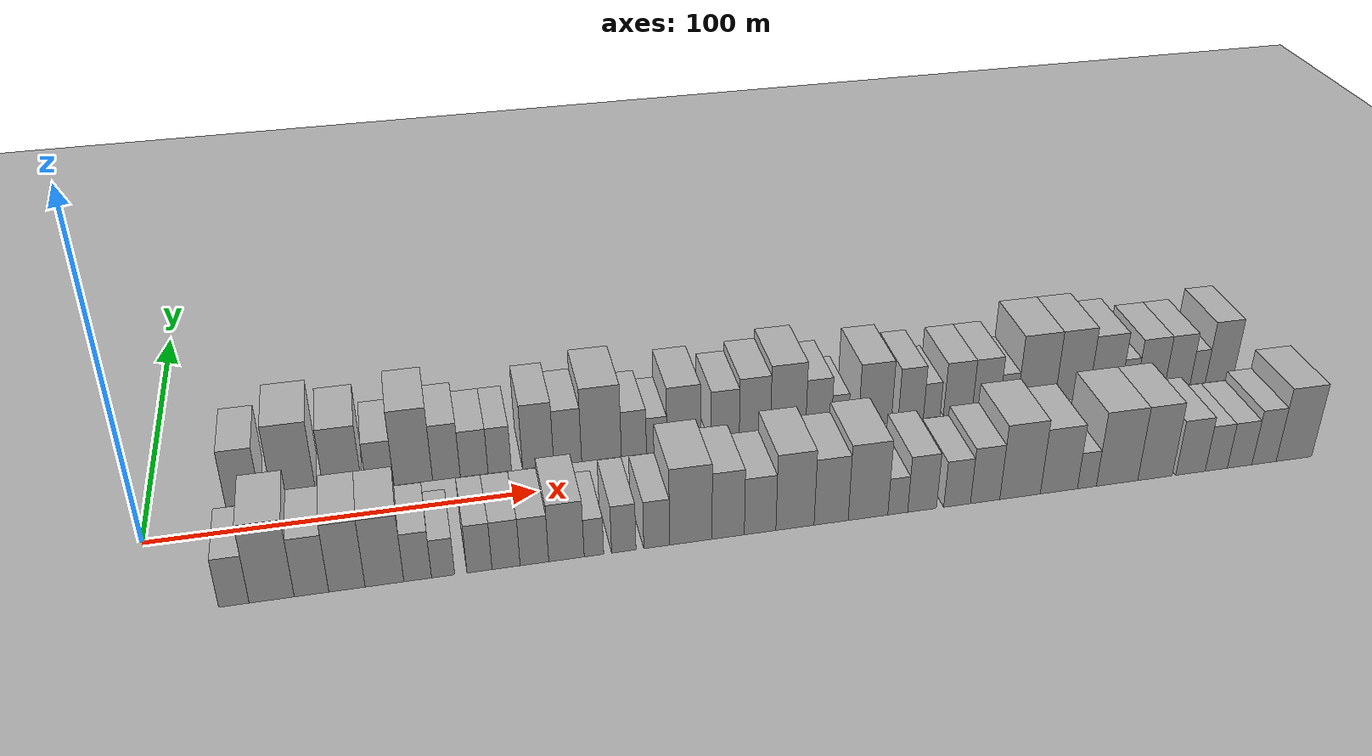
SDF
<?xml version="1.0" encoding="utf-8"?>

<sdf version="1.6">

   <world name="default">

      <gui fullscreen="0">

         <camera name="user_camera">

            <pose>-15 0 4.57585 0 0 0</pose>

            <view_controller>orbit</view_controller>

         </camera>

      </gui>

      <scene>

         <sky>

           <clouds>

             <speed>12</speed>

           </clouds>

         </sky>

         <ambient>0.4 0.4 0.4 1</ambient>

         <background>0.7 0.7 0.7 1</background>

         <shadows>1</shadows>

      </scene>

      <gravity>0 0 -9.8066</gravity>

      <magnetic_field>6e-06 2.3e-05 -4.2e-05</magnetic_field>

      <physics default="0" name="default_physics" type="ode">

         <ode>

            <solver>

               <type>quick</type>

               <iters>10</iters>

               <sor>1.0</sor>

               <use_dynamic_moi_rescaling>0</use_dynamic_moi_rescaling>

            </solver>

            <constraints>

               <cfm>0</cfm>

               <erp>0.2</erp>

               <contact_max_correcting_vel>100</contact_max_correcting_vel>

               <contact_surface_layer>0.001</contact_surface_layer>

            </constraints>

         </ode>

         <max_step_size>0.004</max_step_size>

         <real_time_factor>1</real_time_factor>

         <real_time_update_rate>250</real_time_update_rate>

      </physics>

      <light name="sun" type="directional">

         <cast_shadows>1</cast_shadows>

         <pose>0 0 10 0 0 0</pose>

         <diffuse>0.8 0.8 0.8 1</diffuse>

         <specular>0.2 0.2 0.2 1</specular>

         <attenuation>

            <range>1000</range>

            <constant>0.9</constant>

            <linear>0.01</linear>

            <quadratic>0.001</quadratic>

         </attenuation>

         <direction>-0.5 0.1 -0.9</direction>

      </light>

      <include>

         <name>ground_plane_1</name>

         <uri>model://HANNAS_ground_plane</uri>

         <pose>0 0 0  0 0 0</pose>

      </include>

      <include>

         <name>ground_plane_2</name>

         <uri>model://HANNAS_ground_plane</uri>

         <pose>100 0 0  0 0 0</pose>

      </include>

      <model name="building_1">

         <static>1</static>

         <pose frame="">24.4231 20.0000 0 0.000000 0.000000 1.570796</pose>

         <link name="link">

            <pose frame="">0 0 9.00 0 0 0</pose>

            <collision name="collision">

               <geometry>

                  <box>

                     <size>20.0000 8.8463 18.0000</size>

                  </box>

               </geometry>

               <max_contacts>10</max_contacts>

               <surface>

                  <contact>

                     <ode/>

                  </contact>

                  <bounce/>

                  <friction>

                     <torsional>

                        <ode/>

                     </torsional>

                     <ode/>

                  </friction>

               </surface>

            </collision>

            <visual name="visual">

               <cast_shadows>0</cast_shadows>

               <geometry>

                  <box>

                     <size>20.0000 8.8463 18.0000</size>

                  </box>

               </geometry>

               <material>

                  <script>

                     <uri>model://HANNAS_wall/materials/scripts</uri>

                     <uri>model://HANNAS_wall/materials/textures</uri>

                     <name>vrc/HANNAS_wall</name>

                  </script>

               </material>

            </visual>

            <self_collide>0</self_collide>

            <enable_wind>0</enable_wind>

            <kinematic>0</kinematic>

         </link>

      </model>

      <model name="building_2">

         <static>1</static>

         <pose frame="">37.5085 20.0000 0 0.000000 0.000000 1.570796</pose>

         <link name="link">

            <pose frame="">0 0 12.00 0 0 0</pose>

            <collision name="collision">

               <geometry>

                  <box>

                     <size>20.0000 11.3244 24.0000</size>

                  </box>

               </geometry>

               <max_contacts>10</max_contacts>

               <surface>

                  <contact>

                     <ode/>

                  </contact>

                  <bounce/>

                  <friction>

                     <torsional>

                        <ode/>

                     </torsional>

                     <ode/>

                  </friction>

               </surface>

            </collision>

            <visual name="visual">

               <cast_shadows>0</cast_shadows>

               <geometry>

                  <box>

                     <size>20.0000 11.3244 24.0000</size>

                  </box>

               </geometry>

               <material>

                  <script>

                     <uri>model://HANNAS_wall/materials/scripts</uri>

                     <uri>model://HANNAS_wall/materials/textures</uri>

                     <name>vrc/HANNAS_wall</name>

                  </script>

               </material>

            </visual>

            <self_collide>0</self_collide>

            <enable_wind>0</enable_wind>

            <kinematic>0</kinematic>

         </link>

      </model>

      <model name="building_3">

         <static>1</static>

         <pose frame="">50.1353 20.0000 0 0.000000 0.000000 1.570796</pose>

         <link name="link">

            <pose frame="">0 0 10.50 0 0 0</pose>

            <collision name="collision">

               <geometry>

                  <box>

                     <size>20.0000 9.9292 21.0000</size>

                  </box>

               </geometry>

               <max_contacts>10</max_contacts>

               <surface>

                  <contact>

                     <ode/>

                  </contact>

                  <bounce/>

                  <friction>

                     <torsional>

                        <ode/>

                     </torsional>

                     <ode/>

                  </friction>

               </surface>

            </collision>

            <visual name="visual">

               <cast_shadows>0</cast_shadows>

               <geometry>

                  <box>

                     <size>20.0000 9.9292 21.0000</size>

                  </box>

               </geometry>

               <material>

                  <script>

                     <uri>model://HANNAS_wall/materials/scripts</uri>

                     <uri>model://HANNAS_wall/materials/textures</uri>

                     <name>vrc/HANNAS_wall</name>

                  </script>

               </material>

            </visual>

            <self_collide>0</self_collide>

            <enable_wind>0</enable_wind>

            <kinematic>0</kinematic>

         </link>

      </model>

      <model name="building_4">

         <static>1</static>

         <pose frame="">59.7442 20.0000 0 0.000000 0.000000 1.570796</pose>

         <link name="link">

            <pose frame="">0 0 7.50 0 0 0</pose>

            <collision name="collision">

               <geometry>

                  <box>

                     <size>20.0000 7.2885 15.0000</size>

                  </box>

               </geometry>

               <max_contacts>10</max_contacts>

               <surface>

                  <contact>

                     <ode/>

                  </contact>

                  <bounce/>

                  <friction>

                     <torsional>

                        <ode/>

                     </torsional>

                     <ode/>

                  </friction>

               </surface>

            </collision>

            <visual name="visual">

               <cast_shadows>0</cast_shadows>

               <geometry>

                  <box>

                     <size>20.0000 7.2885 15.0000</size>

                  </box>

               </geometry>

               <material>

                  <script>

                     <uri>model://HANNAS_wall/materials/scripts</uri>

                     <uri>model://HANNAS_wall/materials/textures</uri>

                     <name>vrc/HANNAS_wall</name>

                  </script>

               </material>

            </visual>

            <self_collide>0</self_collide>

            <enable_wind>0</enable_wind>

            <kinematic>0</kinematic>

         </link>

      </model>

      <model name="building_5">

         <static>1</static>

         <pose frame="">68.4696 20.0000 0 0.000000 0.000000 1.570796</pose>

         <link name="link">

            <pose frame="">0 0 12.00 0 0 0</pose>

            <collision name="collision">

               <geometry>

                  <box>

                     <size>20.0000 10.1623 24.0000</size>

                  </box>

               </geometry>

               <max_contacts>10</max_contacts>

               <surface>

                  <contact>

                     <ode/>

                  </contact>

                  <bounce/>

                  <friction>

                     <torsional>

                        <ode/>

                     </torsional>

                     <ode/>

                  </friction>

               </surface>

            </collision>

            <visual name="visual">

               <cast_shadows>0</cast_shadows>

               <geometry>

                  <box>

                     <size>20.0000 10.1623 24.0000</size>

                  </box>

               </geometry>

               <material>

                  <script>

                     <uri>model://HANNAS_wall/materials/scripts</uri>

                     <uri>model://HANNAS_wall/materials/textures</uri>

                     <name>vrc/HANNAS_wall</name>

                  </script>

               </material>

            </visual>

            <self_collide>0</self_collide>

            <enable_wind>0</enable_wind>

            <kinematic>0</kinematic>

         </link>

      </model>

      <model name="building_6">

         <static>1</static>

         <pose frame="">77.2258 20.0000 0 0.000000 0.000000 1.570796</pose>

         <link name="link">

            <pose frame="">0 0 9.00 0 0 0</pose>

            <collision name="collision">

               <geometry>

                  <box>

                     <size>20.0000 7.3500 18.0000</size>

                  </box>

               </geometry>

               <max_contacts>10</max_contacts>

               <surface>

                  <contact>

                     <ode/>

                  </contact>

                  <bounce/>

                  <friction>

                     <torsional>

                        <ode/>

                     </torsional>

                     <ode/>

                  </friction>

               </surface>

            </collision>

            <visual name="visual">

               <cast_shadows>0</cast_shadows>

               <geometry>

                  <box>

                     <size>20.0000 7.3500 18.0000</size>

                  </box>

               </geometry>

               <material>

                  <script>

                     <uri>model://HANNAS_wall/materials/scripts</uri>

                     <uri>model://HANNAS_wall/materials/textures</uri>

                     <name>vrc/HANNAS_wall</name>

                  </script>

               </material>

            </visual>

            <self_collide>0</self_collide>

            <enable_wind>0</enable_wind>

            <kinematic>0</kinematic>

         </link>

      </model>

      <model name="building_7">

         <static>1</static>

         <pose frame="">84.6140 20.0000 0 0.000000 0.000000 1.570796</pose>

         <link name="link">

            <pose frame="">0 0 7.50 0 0 0</pose>

            <collision name="collision">

               <geometry>

                  <box>

                     <size>20.0000 7.4266 15.0000</size>

                  </box>

               </geometry>

               <max_contacts>10</max_contacts>

               <surface>

                  <contact>

                     <ode/>

                  </contact>

                  <bounce/>

                  <friction>

                     <torsional>

                        <ode/>

                     </torsional>

                     <ode/>

                  </friction>

               </surface>

            </collision>

            <visual name="visual">

               <cast_shadows>0</cast_shadows>

               <geometry>

                  <box>

                     <size>20.0000 7.4266 15.0000</size>

                  </box>

               </geometry>

               <material>

                  <script>

                     <uri>model://HANNAS_wall/materials/scripts</uri>

                     <uri>model://HANNAS_wall/materials/textures</uri>

                     <name>vrc/HANNAS_wall</name>

                  </script>

               </material>

            </visual>

            <self_collide>0</self_collide>

            <enable_wind>0</enable_wind>

            <kinematic>0</kinematic>

         </link>

      </model>

      <model name="building_8">

         <static>1</static>

         <pose frame="">91.4693 20.0000 0 0.000000 0.000000 1.570796</pose>

         <link name="link">

            <pose frame="">0 0 7.50 0 0 0</pose>

            <collision name="collision">

               <geometry>

                  <box>

                     <size>20.0000 6.2839 15.0000</size>

                  </box>

               </geometry>

               <max_contacts>10</max_contacts>

               <surface>

                  <contact>

                     <ode/>

                  </contact>

                  <bounce/>

                  <friction>

                     <torsional>

                        <ode/>

                     </torsional>

                     <ode/>

                  </friction>

               </surface>

            </collision>

            <visual name="visual">

               <cast_shadows>0</cast_shadows>

               <geometry>

                  <box>

                     <size>20.0000 6.2839 15.0000</size>

                  </box>

               </geometry>

               <material>

                  <script>

                     <uri>model://HANNAS_wall/materials/scripts</uri>

                     <uri>model://HANNAS_wall/materials/textures</uri>

                     <name>vrc/HANNAS_wall</name>

                  </script>

               </material>

            </visual>

            <self_collide>0</self_collide>

            <enable_wind>0</enable_wind>

            <kinematic>0</kinematic>

         </link>

      </model>

      <model name="building_9">

         <static>1</static>

         <pose frame="">101.8433 20.0000 0 0.000000 0.000000 1.570796</pose>

         <link name="link">

            <pose frame="">0 0 10.50 0 0 0</pose>

            <collision name="collision">

               <geometry>

                  <box>

                     <size>20.0000 8.4641 21.0000</size>

                  </box>

               </geometry>

               <max_contacts>10</max_contacts>

               <surface>

                  <contact>

                     <ode/>

                  </contact>

                  <bounce/>

                  <friction>

                     <torsional>

                        <ode/>

                     </torsional>

                     <ode/>

                  </friction>

               </surface>

            </collision>

            <visual name="visual">

               <cast_shadows>0</cast_shadows>

               <geometry>

                  <box>

                     <size>20.0000 8.4641 21.0000</size>

                  </box>

               </geometry>

               <material>

                  <script>

                     <uri>model://HANNAS_wall/materials/scripts</uri>

                     <uri>model://HANNAS_wall/materials/textures</uri>

                     <name>vrc/HANNAS_wall</name>

                  </script>

               </material>

            </visual>

            <self_collide>0</self_collide>

            <enable_wind>0</enable_wind>

            <kinematic>0</kinematic>

         </link>

      </model>

      <model name="building_10">

         <static>1</static>

         <pose frame="">109.8797 20.0000 0 0.000000 0.000000 1.570796</pose>

         <link name="link">

            <pose frame="">0 0 9.00 0 0 0</pose>

            <collision name="collision">

               <geometry>

                  <box>

                     <size>20.0000 7.6086 18.0000</size>

                  </box>

               </geometry>

               <max_contacts>10</max_contacts>

               <surface>

                  <contact>

                     <ode/>

                  </contact>

                  <bounce/>

                  <friction>

                     <torsional>

                        <ode/>

                     </torsional>

                     <ode/>

                  </friction>

               </surface>

            </collision>

            <visual name="visual">

               <cast_shadows>0</cast_shadows>

               <geometry>

                  <box>

                     <size>20.0000 7.6086 18.0000</size>

                  </box>

               </geometry>

               <material>

                  <script>

                     <uri>model://HANNAS_wall/materials/scripts</uri>

                     <uri>model://HANNAS_wall/materials/textures</uri>

                     <name>vrc/HANNAS_wall</name>

                  </script>

               </material>

            </visual>

            <self_collide>0</self_collide>

            <enable_wind>0</enable_wind>

            <kinematic>0</kinematic>

         </link>

      </model>

      <model name="building_11">

         <static>1</static>

         <pose frame="">119.1592 20.0000 0 0.000000 0.000000 1.570796</pose>

         <link name="link">

            <pose frame="">0 0 12.00 0 0 0</pose>

            <collision name="collision">

               <geometry>

                  <box>

                     <size>20.0000 10.9503 24.0000</size>

                  </box>

               </geometry>

               <max_contacts>10</max_contacts>

               <surface>

                  <contact>

                     <ode/>

                  </contact>

                  <bounce/>

                  <friction>

                     <torsional>

                        <ode/>

                     </torsional>

                     <ode/>

                  </friction>

               </surface>

            </collision>

            <visual name="visual">

               <cast_shadows>0</cast_shadows>

               <geometry>

                  <box>

                     <size>20.0000 10.9503 24.0000</size>

                  </box>

               </geometry>

               <material>

                  <script>

                     <uri>model://HANNAS_wall/materials/scripts</uri>

                     <uri>model://HANNAS_wall/materials/textures</uri>

                     <name>vrc/HANNAS_wall</name>

                  </script>

               </material>

            </visual>

            <self_collide>0</self_collide>

            <enable_wind>0</enable_wind>

            <kinematic>0</kinematic>

         </link>

      </model>

      <model name="building_12">

         <static>1</static>

         <pose frame="">128.1059 20.0000 0 0.000000 0.000000 1.570796</pose>

         <link name="link">

            <pose frame="">0 0 7.50 0 0 0</pose>

            <collision name="collision">

               <geometry>

                  <box>

                     <size>20.0000 6.9432 15.0000</size>

                  </box>

               </geometry>

               <max_contacts>10</max_contacts>

               <surface>

                  <contact>

                     <ode/>

                  </contact>

                  <bounce/>

                  <friction>

                     <torsional>

                        <ode/>

                     </torsional>

                     <ode/>

                  </friction>

               </surface>

            </collision>

            <visual name="visual">

               <cast_shadows>0</cast_shadows>

               <geometry>

                  <box>

                     <size>20.0000 6.9432 15.0000</size>

                  </box>

               </geometry>

               <material>

                  <script>

                     <uri>model://HANNAS_wall/materials/scripts</uri>

                     <uri>model://HANNAS_wall/materials/textures</uri>

                     <name>vrc/HANNAS_wall</name>

                  </script>

               </material>

            </visual>

            <self_collide>0</self_collide>

            <enable_wind>0</enable_wind>

            <kinematic>0</kinematic>

         </link>

      </model>

      <model name="building_13">

         <static>1</static>

         <pose frame="">134.4381 20.0000 0 0.000000 0.000000 1.570796</pose>

         <link name="link">

            <pose frame="">0 0 6.00 0 0 0</pose>

            <collision name="collision">

               <geometry>

                  <box>

                     <size>20.0000 5.7212 12.0000</size>

                  </box>

               </geometry>

               <max_contacts>10</max_contacts>

               <surface>

                  <contact>

                     <ode/>

                  </contact>

                  <bounce/>

                  <friction>

                     <torsional>

                        <ode/>

                     </torsional>

                     <ode/>

                  </friction>

               </surface>

            </collision>

            <visual name="visual">

               <cast_shadows>0</cast_shadows>

               <geometry>

                  <box>

                     <size>20.0000 5.7212 12.0000</size>

                  </box>

               </geometry>

               <material>

                  <script>

                     <uri>model://HANNAS_wall/materials/scripts</uri>

                     <uri>model://HANNAS_wall/materials/textures</uri>

                     <name>vrc/HANNAS_wall</name>

                  </script>

               </material>

            </visual>

            <self_collide>0</self_collide>

            <enable_wind>0</enable_wind>

            <kinematic>0</kinematic>

         </link>

      </model>

      <model name="building_14">

         <static>1</static>

         <pose frame="">142.0085 20.0000 0 0.000000 0.000000 1.570796</pose>

         <link name="link">

            <pose frame="">0 0 10.50 0 0 0</pose>

            <collision name="collision">

               <geometry>

                  <box>

                     <size>20.0000 9.4196 21.0000</size>

                  </box>

               </geometry>

               <max_contacts>10</max_contacts>

               <surface>

                  <contact>

                     <ode/>

                  </contact>

                  <bounce/>

                  <friction>

                     <torsional>

                        <ode/>

                     </torsional>

                     <ode/>

                  </friction>

               </surface>

            </collision>

            <visual name="visual">

               <cast_shadows>0</cast_shadows>

               <geometry>

                  <box>

                     <size>20.0000 9.4196 21.0000</size>

                  </box>

               </geometry>

               <material>

                  <script>

                     <uri>model://HANNAS_wall/materials/scripts</uri>

                     <uri>model://HANNAS_wall/materials/textures</uri>

                     <name>vrc/HANNAS_wall</name>

                  </script>

               </material>

            </visual>

            <self_collide>0</self_collide>

            <enable_wind>0</enable_wind>

            <kinematic>0</kinematic>

         </link>

      </model>

      <model name="building_15">

         <static>1</static>

         <pose frame="">153.6885 20.0000 0 0.000000 0.000000 1.570796</pose>

         <link name="link">

            <pose frame="">0 0 9.00 0 0 0</pose>

            <collision name="collision">

               <geometry>

                  <box>

                     <size>20.0000 7.9404 18.0000</size>

                  </box>

               </geometry>

               <max_contacts>10</max_contacts>

               <surface>

                  <contact>

                     <ode/>

                  </contact>

                  <bounce/>

                  <friction>

                     <torsional>

                        <ode/>

                     </torsional>

                     <ode/>

                  </friction>

               </surface>

            </collision>

            <visual name="visual">

               <cast_shadows>0</cast_shadows>

               <geometry>

                  <box>

                     <size>20.0000 7.9404 18.0000</size>

                  </box>

               </geometry>

               <material>

                  <script>

                     <uri>model://HANNAS_wall/materials/scripts</uri>

                     <uri>model://HANNAS_wall/materials/textures</uri>

                     <name>vrc/HANNAS_wall</name>

                  </script>

               </material>

            </visual>

            <self_collide>0</self_collide>

            <enable_wind>0</enable_wind>

            <kinematic>0</kinematic>

         </link>

      </model>

      <model name="building_16">

         <static>1</static>

         <pose frame="">162.0779 20.0000 0 0.000000 0.000000 1.570796</pose>

         <link name="link">

            <pose frame="">0 0 10.50 0 0 0</pose>

            <collision name="collision">

               <geometry>

                  <box>

                     <size>20.0000 8.8384 21.0000</size>

                  </box>

               </geometry>

               <max_contacts>10</max_contacts>

               <surface>

                  <contact>

                     <ode/>

                  </contact>

                  <bounce/>

                  <friction>

                     <torsional>

                        <ode/>

                     </torsional>

                     <ode/>

                  </friction>

               </surface>

            </collision>

            <visual name="visual">

               <cast_shadows>0</cast_shadows>

               <geometry>

                  <box>

                     <size>20.0000 8.8384 21.0000</size>

                  </box>

               </geometry>

               <material>

                  <script>

                     <uri>model://HANNAS_wall/materials/scripts</uri>

                     <uri>model://HANNAS_wall/materials/textures</uri>

                     <name>vrc/HANNAS_wall</name>

                  </script>

               </material>

            </visual>

            <self_collide>0</self_collide>

            <enable_wind>0</enable_wind>

            <kinematic>0</kinematic>

         </link>

      </model>

      <model name="building_17">

         <static>1</static>

         <pose frame="">171.5769 20.0000 0 0.000000 0.000000 1.570796</pose>

         <link name="link">

            <pose frame="">0 0 12.00 0 0 0</pose>

            <collision name="collision">

               <geometry>

                  <box>

                     <size>20.0000 10.1597 24.0000</size>

                  </box>

               </geometry>

               <max_contacts>10</max_contacts>

               <surface>

                  <contact>

                     <ode/>

                  </contact>

                  <bounce/>

                  <friction>

                     <torsional>

                        <ode/>

                     </torsional>

                     <ode/>

                  </friction>

               </surface>

            </collision>

            <visual name="visual">

               <cast_shadows>0</cast_shadows>

               <geometry>

                  <box>

                     <size>20.0000 10.1597 24.0000</size>

                  </box>

               </geometry>

               <material>

                  <script>

                     <uri>model://HANNAS_wall/materials/scripts</uri>

                     <uri>model://HANNAS_wall/materials/textures</uri>

                     <name>vrc/HANNAS_wall</name>

                  </script>

               </material>

            </visual>

            <self_collide>0</self_collide>

            <enable_wind>0</enable_wind>

            <kinematic>0</kinematic>

         </link>

      </model>

      <model name="building_18">

         <static>1</static>

         <pose frame="">180.3827 20.0000 0 0.000000 0.000000 1.570796</pose>

         <link name="link">

            <pose frame="">0 0 9.00 0 0 0</pose>

            <collision name="collision">

               <geometry>

                  <box>

                     <size>20.0000 7.4519 18.0000</size>

                  </box>

               </geometry>

               <max_contacts>10</max_contacts>

               <surface>

                  <contact>

                     <ode/>

                  </contact>

                  <bounce/>

                  <friction>

                     <torsional>

                        <ode/>

                     </torsional>

                     <ode/>

                  </friction>

               </surface>

            </collision>

            <visual name="visual">

               <cast_shadows>0</cast_shadows>

               <geometry>

                  <box>

                     <size>20.0000 7.4519 18.0000</size>

                  </box>

               </geometry>

               <material>

                  <script>

                     <uri>model://HANNAS_wall/materials/scripts</uri>

                     <uri>model://HANNAS_wall/materials/textures</uri>

                     <name>vrc/HANNAS_wall</name>

                  </script>

               </material>

            </visual>

            <self_collide>0</self_collide>

            <enable_wind>0</enable_wind>

            <kinematic>0</kinematic>

         </link>

      </model>

      <model name="building_19">

         <static>1</static>

         <pose frame="">186.5635 20.0000 0 0.000000 0.000000 1.570796</pose>

         <link name="link">

            <pose frame="">0 0 6.00 0 0 0</pose>

            <collision name="collision">

               <geometry>

                  <box>

                     <size>20.0000 4.9098 12.0000</size>

                  </box>

               </geometry>

               <max_contacts>10</max_contacts>

               <surface>

                  <contact>

                     <ode/>

                  </contact>

                  <bounce/>

                  <friction>

                     <torsional>

                        <ode/>

                     </torsional>

                     <ode/>

                  </friction>

               </surface>

            </collision>

            <visual name="visual">

               <cast_shadows>0</cast_shadows>

               <geometry>

                  <box>

                     <size>20.0000 4.9098 12.0000</size>

                  </box>

               </geometry>

               <material>

                  <script>

                     <uri>model://HANNAS_wall/materials/scripts</uri>

                     <uri>model://HANNAS_wall/materials/textures</uri>

                     <name>vrc/HANNAS_wall</name>

                  </script>

               </material>

            </visual>

            <self_collide>0</self_collide>

            <enable_wind>0</enable_wind>

            <kinematic>0</kinematic>

         </link>

      </model>

      <model name="building_20">

         <static>1</static>

         <pose frame="">196.8734 20.0000 0 0.000000 0.000000 1.570796</pose>

         <link name="link">

            <pose frame="">0 0 10.50 0 0 0</pose>

            <collision name="collision">

               <geometry>

                  <box>

                     <size>20.0000 9.7098 21.0000</size>

                  </box>

               </geometry>

               <max_contacts>10</max_contacts>

               <surface>

                  <contact>

                     <ode/>

                  </contact>

                  <bounce/>

                  <friction>

                     <torsional>

                        <ode/>

                     </torsional>

                     <ode/>

                  </friction>

               </surface>

            </collision>

            <visual name="visual">

               <cast_shadows>0</cast_shadows>

               <geometry>

                  <box>

                     <size>20.0000 9.7098 21.0000</size>

                  </box>

               </geometry>

               <material>

                  <script>

                     <uri>model://HANNAS_wall/materials/scripts</uri>

                     <uri>model://HANNAS_wall/materials/textures</uri>

                     <name>vrc/HANNAS_wall</name>

                  </script>

               </material>

            </visual>

            <self_collide>0</self_collide>

            <enable_wind>0</enable_wind>

            <kinematic>0</kinematic>

         </link>

      </model>

      <model name="building_21">

         <static>1</static>

         <pose frame="">207.4792 20.0000 0 0.000000 0.000000 1.570796</pose>

         <link name="link">

            <pose frame="">0 0 9.00 0 0 0</pose>

            <collision name="collision">

               <geometry>

                  <box>

                     <size>20.0000 7.5019 18.0000</size>

                  </box>

               </geometry>

               <max_contacts>10</max_contacts>

               <surface>

                  <contact>

                     <ode/>

                  </contact>

                  <bounce/>

                  <friction>

                     <torsional>

                        <ode/>

                     </torsional>

                     <ode/>

                  </friction>

               </surface>

            </collision>

            <visual name="visual">

               <cast_shadows>0</cast_shadows>

               <geometry>

                  <box>

                     <size>20.0000 7.5019 18.0000</size>

                  </box>

               </geometry>

               <material>

                  <script>

                     <uri>model://HANNAS_wall/materials/scripts</uri>

                     <uri>model://HANNAS_wall/materials/textures</uri>

                     <name>vrc/HANNAS_wall</name>

                  </script>

               </material>

            </visual>

            <self_collide>0</self_collide>

            <enable_wind>0</enable_wind>

            <kinematic>0</kinematic>

         </link>

      </model>

      <model name="building_22">

         <static>1</static>

         <pose frame="">213.7127 20.0000 0 0.000000 0.000000 1.570796</pose>

         <link name="link">

            <pose frame="">0 0 6.00 0 0 0</pose>

            <collision name="collision">

               <geometry>

                  <box>

                     <size>20.0000 4.9652 12.0000</size>

                  </box>

               </geometry>

               <max_contacts>10</max_contacts>

               <surface>

                  <contact>

                     <ode/>

                  </contact>

                  <bounce/>

                  <friction>

                     <torsional>

                        <ode/>

                     </torsional>

                     <ode/>

                  </friction>

               </surface>

            </collision>

            <visual name="visual">

               <cast_shadows>0</cast_shadows>

               <geometry>

                  <box>

                     <size>20.0000 4.9652 12.0000</size>

                  </box>

               </geometry>

               <material>

                  <script>

                     <uri>model://HANNAS_wall/materials/scripts</uri>

                     <uri>model://HANNAS_wall/materials/textures</uri>

                     <name>vrc/HANNAS_wall</name>

                  </script>

               </material>

            </visual>

            <self_collide>0</self_collide>

            <enable_wind>0</enable_wind>

            <kinematic>0</kinematic>

         </link>

      </model>

      <model name="building_23">

         <static>1</static>

         <pose frame="">221.4947 20.0000 0 0.000000 0.000000 1.570796</pose>

         <link name="link">

            <pose frame="">0 0 9.00 0 0 0</pose>

            <collision name="collision">

               <geometry>

                  <box>

                     <size>20.0000 8.5988 18.0000</size>

                  </box>

               </geometry>

               <max_contacts>10</max_contacts>

               <surface>

                  <contact>

                     <ode/>

                  </contact>

                  <bounce/>

                  <friction>

                     <torsional>

                        <ode/>

                     </torsional>

                     <ode/>

                  </friction>

               </surface>

            </collision>

            <visual name="visual">

               <cast_shadows>0</cast_shadows>

               <geometry>

                  <box>

                     <size>20.0000 8.5988 18.0000</size>

                  </box>

               </geometry>

               <material>

                  <script>

                     <uri>model://HANNAS_wall/materials/scripts</uri>

                     <uri>model://HANNAS_wall/materials/textures</uri>

                     <name>vrc/HANNAS_wall</name>

                  </script>

               </material>

            </visual>

            <self_collide>0</self_collide>

            <enable_wind>0</enable_wind>

            <kinematic>0</kinematic>

         </link>

      </model>

      <model name="building_24">

         <static>1</static>

         <pose frame="">229.9302 20.0000 0 0.000000 0.000000 1.570796</pose>

         <link name="link">

            <pose frame="">0 0 9.00 0 0 0</pose>

            <collision name="collision">

               <geometry>

                  <box>

                     <size>20.0000 8.2722 18.0000</size>

                  </box>

               </geometry>

               <max_contacts>10</max_contacts>

               <surface>

                  <contact>

                     <ode/>

                  </contact>

                  <bounce/>

                  <friction>

                     <torsional>

                        <ode/>

                     </torsional>

                     <ode/>

                  </friction>

               </surface>

            </collision>

            <visual name="visual">

               <cast_shadows>0</cast_shadows>

               <geometry>

                  <box>

                     <size>20.0000 8.2722 18.0000</size>

                  </box>

               </geometry>

               <material>

                  <script>

                     <uri>model://HANNAS_wall/materials/scripts</uri>

                     <uri>model://HANNAS_wall/materials/textures</uri>

                     <name>vrc/HANNAS_wall</name>

                  </script>

               </material>

            </visual>

            <self_collide>0</self_collide>

            <enable_wind>0</enable_wind>

            <kinematic>0</kinematic>

         </link>

      </model>

      <model name="building_25">

         <static>1</static>

         <pose frame="">236.7122 20.0000 0 0.000000 0.000000 1.570796</pose>

         <link name="link">

            <pose frame="">0 0 6.00 0 0 0</pose>

            <collision name="collision">

               <geometry>

                  <box>

                     <size>20.0000 5.2917 12.0000</size>

                  </box>

               </geometry>

               <max_contacts>10</max_contacts>

               <surface>

                  <contact>

                     <ode/>

                  </contact>

                  <bounce/>

                  <friction>

                     <torsional>

                        <ode/>

                     </torsional>

                     <ode/>

                  </friction>

               </surface>

            </collision>

            <visual name="visual">

               <cast_shadows>0</cast_shadows>

               <geometry>

                  <box>

                     <size>20.0000 5.2917 12.0000</size>

                  </box>

               </geometry>

               <material>

                  <script>

                     <uri>model://HANNAS_wall/materials/scripts</uri>

                     <uri>model://HANNAS_wall/materials/textures</uri>

                     <name>vrc/HANNAS_wall</name>

                  </script>

               </material>

            </visual>

            <self_collide>0</self_collide>

            <enable_wind>0</enable_wind>

            <kinematic>0</kinematic>

         </link>

      </model>

      <model name="building_26">

         <static>1</static>

         <pose frame="">245.1382 20.0000 0 0.000000 0.000000 1.570796</pose>

         <link name="link">

            <pose frame="">0 0 12.00 0 0 0</pose>

            <collision name="collision">

               <geometry>

                  <box>

                     <size>20.0000 11.5604 24.0000</size>

                  </box>

               </geometry>

               <max_contacts>10</max_contacts>

               <surface>

                  <contact>

                     <ode/>

                  </contact>

                  <bounce/>

                  <friction>

                     <torsional>

                        <ode/>

                     </torsional>

                     <ode/>

                  </friction>

               </surface>

            </collision>

            <visual name="visual">

               <cast_shadows>0</cast_shadows>

               <geometry>

                  <box>

                     <size>20.0000 11.5604 24.0000</size>

                  </box>

               </geometry>

               <material>

                  <script>

                     <uri>model://HANNAS_wall/materials/scripts</uri>

                     <uri>model://HANNAS_wall/materials/textures</uri>

                     <name>vrc/HANNAS_wall</name>

                  </script>

               </material>

            </visual>

            <self_collide>0</self_collide>

            <enable_wind>0</enable_wind>

            <kinematic>0</kinematic>

         </link>

      </model>

      <model name="building_27">

         <static>1</static>

         <pose frame="">256.1483 20.0000 0 0.000000 0.000000 1.570796</pose>

         <link name="link">

            <pose frame="">0 0 12.00 0 0 0</pose>

            <collision name="collision">

               <geometry>

                  <box>

                     <size>20.0000 10.4598 24.0000</size>

                  </box>

               </geometry>

               <max_contacts>10</max_contacts>

               <surface>

                  <contact>

                     <ode/>

                  </contact>

                  <bounce/>

                  <friction>

                     <torsional>

                        <ode/>

                     </torsional>

                     <ode/>

                  </friction>

               </surface>

            </collision>

            <visual name="visual">

               <cast_shadows>0</cast_shadows>

               <geometry>

                  <box>

                     <size>20.0000 10.4598 24.0000</size>

                  </box>

               </geometry>

               <material>

                  <script>

                     <uri>model://HANNAS_wall/materials/scripts</uri>

                     <uri>model://HANNAS_wall/materials/textures</uri>

                     <name>vrc/HANNAS_wall</name>

                  </script>

               </material>

            </visual>

            <self_collide>0</self_collide>

            <enable_wind>0</enable_wind>

            <kinematic>0</kinematic>

         </link>

      </model>

      <model name="building_28">

         <static>1</static>

         <pose frame="">266.3524 20.0000 0 0.000000 0.000000 1.570796</pose>

         <link name="link">

            <pose frame="">0 0 10.50 0 0 0</pose>

            <collision name="collision">

               <geometry>

                  <box>

                     <size>20.0000 9.9483 21.0000</size>

                  </box>

               </geometry>

               <max_contacts>10</max_contacts>

               <surface>

                  <contact>

                     <ode/>

                  </contact>

                  <bounce/>

                  <friction>

                     <torsional>

                        <ode/>

                     </torsional>

                     <ode/>

                  </friction>

               </surface>

            </collision>

            <visual name="visual">

               <cast_shadows>0</cast_shadows>

               <geometry>

                  <box>

                     <size>20.0000 9.9483 21.0000</size>

                  </box>

               </geometry>

               <material>

                  <script>

                     <uri>model://HANNAS_wall/materials/scripts</uri>

                     <uri>model://HANNAS_wall/materials/textures</uri>

                     <name>vrc/HANNAS_wall</name>

                  </script>

               </material>

            </visual>

            <self_collide>0</self_collide>

            <enable_wind>0</enable_wind>

            <kinematic>0</kinematic>

         </link>

      </model>

      <model name="building_29">

         <static>1</static>

         <pose frame="">273.7515 20.0000 0 0.000000 0.000000 1.570796</pose>

         <link name="link">

            <pose frame="">0 0 6.00 0 0 0</pose>

            <collision name="collision">

               <geometry>

                  <box>

                     <size>20.0000 4.8498 12.0000</size>

                  </box>

               </geometry>

               <max_contacts>10</max_contacts>

               <surface>

                  <contact>

                     <ode/>

                  </contact>

                  <bounce/>

                  <friction>

                     <torsional>

                        <ode/>

                     </torsional>

                     <ode/>

                  </friction>

               </surface>

            </collision>

            <visual name="visual">

               <cast_shadows>0</cast_shadows>

               <geometry>

                  <box>

                     <size>20.0000 4.8498 12.0000</size>

                  </box>

               </geometry>

               <material>

                  <script>

                     <uri>model://HANNAS_wall/materials/scripts</uri>

                     <uri>model://HANNAS_wall/materials/textures</uri>

                     <name>vrc/HANNAS_wall</name>

                  </script>

               </material>

            </visual>

            <self_collide>0</self_collide>

            <enable_wind>0</enable_wind>

            <kinematic>0</kinematic>

         </link>

      </model>

      <model name="building_30">

         <static>1</static>

         <pose frame="">280.6696 20.0000 0 0.000000 0.000000 1.570796</pose>

         <link name="link">

            <pose frame="">0 0 9.00 0 0 0</pose>

            <collision name="collision">

               <geometry>

                  <box>

                     <size>20.0000 8.9865 18.0000</size>

                  </box>

               </geometry>

               <max_contacts>10</max_contacts>

               <surface>

                  <contact>

                     <ode/>

                  </contact>

                  <bounce/>

                  <friction>

                     <torsional>

                        <ode/>

                     </torsional>

                     <ode/>

                  </friction>

               </surface>

            </collision>

            <visual name="visual">

               <cast_shadows>0</cast_shadows>

               <geometry>

                  <box>

                     <size>20.0000 8.9865 18.0000</size>

                  </box>

               </geometry>

               <material>

                  <script>

                     <uri>model://HANNAS_wall/materials/scripts</uri>

                     <uri>model://HANNAS_wall/materials/textures</uri>

                     <name>vrc/HANNAS_wall</name>

                  </script>

               </material>

            </visual>

            <self_collide>0</self_collide>

            <enable_wind>0</enable_wind>

            <kinematic>0</kinematic>

         </link>

      </model>

      <model name="building_31">

         <static>1</static>

         <pose frame="">289.2154 20.0000 0 0.000000 0.000000 1.570796</pose>

         <link name="link">

            <pose frame="">0 0 9.00 0 0 0</pose>

            <collision name="collision">

               <geometry>

                  <box>

                     <size>20.0000 8.1050 18.0000</size>

                  </box>

               </geometry>

               <max_contacts>10</max_contacts>

               <surface>

                  <contact>

                     <ode/>

                  </contact>

                  <bounce/>

                  <friction>

                     <torsional>

                        <ode/>

                     </torsional>

                     <ode/>

                  </friction>

               </surface>

            </collision>

            <visual name="visual">

               <cast_shadows>0</cast_shadows>

               <geometry>

                  <box>

                     <size>20.0000 8.1050 18.0000</size>

                  </box>

               </geometry>

               <material>

                  <script>

                     <uri>model://HANNAS_wall/materials/scripts</uri>

                     <uri>model://HANNAS_wall/materials/textures</uri>

                     <name>vrc/HANNAS_wall</name>

                  </script>

               </material>

            </visual>

            <self_collide>0</self_collide>

            <enable_wind>0</enable_wind>

            <kinematic>0</kinematic>

         </link>

      </model>

      <model name="building_32">

         <static>1</static>

         <pose frame="">295.6889 20.0000 0 0.000000 0.000000 1.570796</pose>

         <link name="link">

            <pose frame="">0 0 6.00 0 0 0</pose>

            <collision name="collision">

               <geometry>

                  <box>

                     <size>20.0000 4.8420 12.0000</size>

                  </box>

               </geometry>

               <max_contacts>10</max_contacts>

               <surface>

                  <contact>

                     <ode/>

                  </contact>

                  <bounce/>

                  <friction>

                     <torsional>

                        <ode/>

                     </torsional>

                     <ode/>

                  </friction>

               </surface>

            </collision>

            <visual name="visual">

               <cast_shadows>0</cast_shadows>

               <geometry>

                  <box>

                     <size>20.0000 4.8420 12.0000</size>

                  </box>

               </geometry>

               <material>

                  <script>

                     <uri>model://HANNAS_wall/materials/scripts</uri>

                     <uri>model://HANNAS_wall/materials/textures</uri>

                     <name>vrc/HANNAS_wall</name>

                  </script>

               </material>

            </visual>

            <self_collide>0</self_collide>

            <enable_wind>0</enable_wind>

            <kinematic>0</kinematic>

         </link>

      </model>

      <model name="building_33">

         <static>1</static>

         <pose frame="">302.5286 20.0000 0 0.000000 0.000000 1.570796</pose>

         <link name="link">

            <pose frame="">0 0 10.50 0 0 0</pose>

            <collision name="collision">

               <geometry>

                  <box>

                     <size>20.0000 8.8374 21.0000</size>

                  </box>

               </geometry>

               <max_contacts>10</max_contacts>

               <surface>

                  <contact>

                     <ode/>

                  </contact>

                  <bounce/>

                  <friction>

                     <torsional>

                        <ode/>

                     </torsional>

                     <ode/>

                  </friction>

               </surface>

            </collision>

            <visual name="visual">

               <cast_shadows>0</cast_shadows>

               <geometry>

                  <box>

                     <size>20.0000 8.8374 21.0000</size>

                  </box>

               </geometry>

               <material>

                  <script>

                     <uri>model://HANNAS_wall/materials/scripts</uri>

                     <uri>model://HANNAS_wall/materials/textures</uri>

                     <name>vrc/HANNAS_wall</name>

                  </script>

               </material>

            </visual>

            <self_collide>0</self_collide>

            <enable_wind>0</enable_wind>

            <kinematic>0</kinematic>

         </link>

      </model>

      <model name="building_34">

         <static>1</static>

         <pose frame="">23.5488 -20.0000 0 0.000000 0.000000 1.570796</pose>

         <link name="link">

            <pose frame="">0 0 7.50 0 0 0</pose>

            <collision name="collision">

               <geometry>

                  <box>

                     <size>20.0000 7.0976 15.0000</size>

                  </box>

               </geometry>

               <max_contacts>10</max_contacts>

               <surface>

                  <contact>

                     <ode/>

                  </contact>

                  <bounce/>

                  <friction>

                     <torsional>

                        <ode/>

                     </torsional>

                     <ode/>

                  </friction>

               </surface>

            </collision>

            <visual name="visual">

               <cast_shadows>0</cast_shadows>

               <geometry>

                  <box>

                     <size>20.0000 7.0976 15.0000</size>

                  </box>

               </geometry>

               <material>

                  <script>

                     <uri>model://HANNAS_wall/materials/scripts</uri>

                     <uri>model://HANNAS_wall/materials/textures</uri>

                     <name>vrc/HANNAS_wall</name>

                  </script>

               </material>

            </visual>

            <self_collide>0</self_collide>

            <enable_wind>0</enable_wind>

            <kinematic>0</kinematic>

         </link>

      </model>

      <model name="building_35">

         <static>1</static>

         <pose frame="">32.3856 -20.0000 0 0.000000 0.000000 1.570796</pose>

         <link name="link">

            <pose frame="">0 0 12.00 0 0 0</pose>

            <collision name="collision">

               <geometry>

                  <box>

                     <size>20.0000 10.5759 24.0000</size>

                  </box>

               </geometry>

               <max_contacts>10</max_contacts>

               <surface>

                  <contact>

                     <ode/>

                  </contact>

                  <bounce/>

                  <friction>

                     <torsional>

                        <ode/>

                     </torsional>

                     <ode/>

                  </friction>

               </surface>

            </collision>

            <visual name="visual">

               <cast_shadows>0</cast_shadows>

               <geometry>

                  <box>

                     <size>20.0000 10.5759 24.0000</size>

                  </box>

               </geometry>

               <material>

                  <script>

                     <uri>model://HANNAS_wall/materials/scripts</uri>

                     <uri>model://HANNAS_wall/materials/textures</uri>

                     <name>vrc/HANNAS_wall</name>

                  </script>

               </material>

            </visual>

            <self_collide>0</self_collide>

            <enable_wind>0</enable_wind>

            <kinematic>0</kinematic>

         </link>

      </model>

      <model name="building_36">

         <static>1</static>

         <pose frame="">41.7662 -20.0000 0 0.000000 0.000000 1.570796</pose>

         <link name="link">

            <pose frame="">0 0 9.00 0 0 0</pose>

            <collision name="collision">

               <geometry>

                  <box>

                     <size>20.0000 8.1854 18.0000</size>

                  </box>

               </geometry>

               <max_contacts>10</max_contacts>

               <surface>

                  <contact>

                     <ode/>

                  </contact>

                  <bounce/>

                  <friction>

                     <torsional>

                        <ode/>

                     </torsional>

                     <ode/>

                  </friction>

               </surface>

            </collision>

            <visual name="visual">

               <cast_shadows>0</cast_shadows>

               <geometry>

                  <box>

                     <size>20.0000 8.1854 18.0000</size>

                  </box>

               </geometry>

               <material>

                  <script>

                     <uri>model://HANNAS_wall/materials/scripts</uri>

                     <uri>model://HANNAS_wall/materials/textures</uri>

                     <name>vrc/HANNAS_wall</name>

                  </script>

               </material>

            </visual>

            <self_collide>0</self_collide>

            <enable_wind>0</enable_wind>

            <kinematic>0</kinematic>

         </link>

      </model>

      <model name="building_37">

         <static>1</static>

         <pose frame="">50.1819 -20.0000 0 0.000000 0.000000 1.570796</pose>

         <link name="link">

            <pose frame="">0 0 10.50 0 0 0</pose>

            <collision name="collision">

               <geometry>

                  <box>

                     <size>20.0000 8.6461 21.0000</size>

                  </box>

               </geometry>

               <max_contacts>10</max_contacts>

               <surface>

                  <contact>

                     <ode/>

                  </contact>

                  <bounce/>

                  <friction>

                     <torsional>

                        <ode/>

                     </torsional>

                     <ode/>

                  </friction>

               </surface>

            </collision>

            <visual name="visual">

               <cast_shadows>0</cast_shadows>

               <geometry>

                  <box>

                     <size>20.0000 8.6461 21.0000</size>

                  </box>

               </geometry>

               <material>

                  <script>

                     <uri>model://HANNAS_wall/materials/scripts</uri>

                     <uri>model://HANNAS_wall/materials/textures</uri>

                     <name>vrc/HANNAS_wall</name>

                  </script>

               </material>

            </visual>

            <self_collide>0</self_collide>

            <enable_wind>0</enable_wind>

            <kinematic>0</kinematic>

         </link>

      </model>

      <model name="building_38">

         <static>1</static>

         <pose frame="">59.1694 -20.0000 0 0.000000 0.000000 1.570796</pose>

         <link name="link">

            <pose frame="">0 0 10.50 0 0 0</pose>

            <collision name="collision">

               <geometry>

                  <box>

                     <size>20.0000 9.3289 21.0000</size>

                  </box>

               </geometry>

               <max_contacts>10</max_contacts>

               <surface>

                  <contact>

                     <ode/>

                  </contact>

                  <bounce/>

                  <friction>

                     <torsional>

                        <ode/>

                     </torsional>

                     <ode/>

                  </friction>

               </surface>

            </collision>

            <visual name="visual">

               <cast_shadows>0</cast_shadows>

               <geometry>

                  <box>

                     <size>20.0000 9.3289 21.0000</size>

                  </box>

               </geometry>

               <material>

                  <script>

                     <uri>model://HANNAS_wall/materials/scripts</uri>

                     <uri>model://HANNAS_wall/materials/textures</uri>

                     <name>vrc/HANNAS_wall</name>

                  </script>

               </material>

            </visual>

            <self_collide>0</self_collide>

            <enable_wind>0</enable_wind>

            <kinematic>0</kinematic>

         </link>

      </model>

      <model name="building_39">

         <static>1</static>

         <pose frame="">67.1872 -20.0000 0 0.000000 0.000000 1.570796</pose>

         <link name="link">

            <pose frame="">0 0 7.50 0 0 0</pose>

            <collision name="collision">

               <geometry>

                  <box>

                     <size>20.0000 6.7068 15.0000</size>

                  </box>

               </geometry>

               <max_contacts>10</max_contacts>

               <surface>

                  <contact>

                     <ode/>

                  </contact>

                  <bounce/>

                  <friction>

                     <torsional>

                        <ode/>

                     </torsional>

                     <ode/>

                  </friction>

               </surface>

            </collision>

            <visual name="visual">

               <cast_shadows>0</cast_shadows>

               <geometry>

                  <box>

                     <size>20.0000 6.7068 15.0000</size>

                  </box>

               </geometry>

               <material>

                  <script>

                     <uri>model://HANNAS_wall/materials/scripts</uri>

                     <uri>model://HANNAS_wall/materials/textures</uri>

                     <name>vrc/HANNAS_wall</name>

                  </script>

               </material>

            </visual>

            <self_collide>0</self_collide>

            <enable_wind>0</enable_wind>

            <kinematic>0</kinematic>

         </link>

      </model>

      <model name="building_40">

         <static>1</static>

         <pose frame="">73.3599 -20.0000 0 0.000000 0.000000 1.570796</pose>

         <link name="link">

            <pose frame="">0 0 6.00 0 0 0</pose>

            <collision name="collision">

               <geometry>

                  <box>

                     <size>20.0000 5.6386 12.0000</size>

                  </box>

               </geometry>

               <max_contacts>10</max_contacts>

               <surface>

                  <contact>

                     <ode/>

                  </contact>

                  <bounce/>

                  <friction>

                     <torsional>

                        <ode/>

                     </torsional>

                     <ode/>

                  </friction>

               </surface>

            </collision>

            <visual name="visual">

               <cast_shadows>0</cast_shadows>

               <geometry>

                  <box>

                     <size>20.0000 5.6386 12.0000</size>

                  </box>

               </geometry>

               <material>

                  <script>

                     <uri>model://HANNAS_wall/materials/scripts</uri>

                     <uri>model://HANNAS_wall/materials/textures</uri>

                     <name>vrc/HANNAS_wall</name>

                  </script>

               </material>

            </visual>

            <self_collide>0</self_collide>

            <enable_wind>0</enable_wind>

            <kinematic>0</kinematic>

         </link>

      </model>

      <model name="building_41">

         <static>1</static>

         <pose frame="">82.2640 -20.0000 0 0.000000 0.000000 1.570796</pose>

         <link name="link">

            <pose frame="">0 0 7.50 0 0 0</pose>

            <collision name="collision">

               <geometry>

                  <box>

                     <size>20.0000 6.1696 15.0000</size>

                  </box>

               </geometry>

               <max_contacts>10</max_contacts>

               <surface>

                  <contact>

                     <ode/>

                  </contact>

                  <bounce/>

                  <friction>

                     <torsional>

                        <ode/>

                     </torsional>

                     <ode/>

                  </friction>

               </surface>

            </collision>

            <visual name="visual">

               <cast_shadows>0</cast_shadows>

               <geometry>

                  <box>

                     <size>20.0000 6.1696 15.0000</size>

                  </box>

               </geometry>

               <material>

                  <script>

                     <uri>model://HANNAS_wall/materials/scripts</uri>

                     <uri>model://HANNAS_wall/materials/textures</uri>

                     <name>vrc/HANNAS_wall</name>

                  </script>

               </material>

            </visual>

            <self_collide>0</self_collide>

            <enable_wind>0</enable_wind>

            <kinematic>0</kinematic>

         </link>

      </model>

      <model name="building_42">

         <static>1</static>

         <pose frame="">88.8178 -20.0000 0 0.000000 0.000000 1.570796</pose>

         <link name="link">

            <pose frame="">0 0 7.50 0 0 0</pose>

            <collision name="collision">

               <geometry>

                  <box>

                     <size>20.0000 6.9380 15.0000</size>

                  </box>

               </geometry>

               <max_contacts>10</max_contacts>

               <surface>

                  <contact>

                     <ode/>

                  </contact>

                  <bounce/>

                  <friction>

                     <torsional>

                        <ode/>

                     </torsional>

                     <ode/>

                  </friction>

               </surface>

            </collision>

            <visual name="visual">

               <cast_shadows>0</cast_shadows>

               <geometry>

                  <box>

                     <size>20.0000 6.9380 15.0000</size>

                  </box>

               </geometry>

               <material>

                  <script>

                     <uri>model://HANNAS_wall/materials/scripts</uri>

                     <uri>model://HANNAS_wall/materials/textures</uri>

                     <name>vrc/HANNAS_wall</name>

                  </script>

               </material>

            </visual>

            <self_collide>0</self_collide>

            <enable_wind>0</enable_wind>

            <kinematic>0</kinematic>

         </link>

      </model>

      <model name="building_43">

         <static>1</static>

         <pose frame="">95.8531 -20.0000 0 0.000000 0.000000 1.570796</pose>

         <link name="link">

            <pose frame="">0 0 7.50 0 0 0</pose>

            <collision name="collision">

               <geometry>

                  <box>

                     <size>20.0000 7.1326 15.0000</size>

                  </box>

               </geometry>

               <max_contacts>10</max_contacts>

               <surface>

                  <contact>

                     <ode/>

                  </contact>

                  <bounce/>

                  <friction>

                     <torsional>

                        <ode/>

                     </torsional>

                     <ode/>

                  </friction>

               </surface>

            </collision>

            <visual name="visual">

               <cast_shadows>0</cast_shadows>

               <geometry>

                  <box>

                     <size>20.0000 7.1326 15.0000</size>

                  </box>

               </geometry>

               <material>

                  <script>

                     <uri>model://HANNAS_wall/materials/scripts</uri>

                     <uri>model://HANNAS_wall/materials/textures</uri>

                     <name>vrc/HANNAS_wall</name>

                  </script>

               </material>

            </visual>

            <self_collide>0</self_collide>

            <enable_wind>0</enable_wind>

            <kinematic>0</kinematic>

         </link>

      </model>

      <model name="building_44">

         <static>1</static>

         <pose frame="">103.8704 -20.0000 0 0.000000 0.000000 1.570796</pose>

         <link name="link">

            <pose frame="">0 0 9.00 0 0 0</pose>

            <collision name="collision">

               <geometry>

                  <box>

                     <size>20.0000 8.9021 18.0000</size>

                  </box>

               </geometry>

               <max_contacts>10</max_contacts>

               <surface>

                  <contact>

                     <ode/>

                  </contact>

                  <bounce/>

                  <friction>

                     <torsional>

                        <ode/>

                     </torsional>

                     <ode/>

                  </friction>

               </surface>

            </collision>

            <visual name="visual">

               <cast_shadows>0</cast_shadows>

               <geometry>

                  <box>

                     <size>20.0000 8.9021 18.0000</size>

                  </box>

               </geometry>

               <material>

                  <script>

                     <uri>model://HANNAS_wall/materials/scripts</uri>

                     <uri>model://HANNAS_wall/materials/textures</uri>

                     <name>vrc/HANNAS_wall</name>

                  </script>

               </material>

            </visual>

            <self_collide>0</self_collide>

            <enable_wind>0</enable_wind>

            <kinematic>0</kinematic>

         </link>

      </model>

      <model name="building_45">

         <static>1</static>

         <pose frame="">110.7804 -20.0000 0 0.000000 0.000000 1.570796</pose>

         <link name="link">

            <pose frame="">0 0 6.00 0 0 0</pose>

            <collision name="collision">

               <geometry>

                  <box>

                     <size>20.0000 4.9178 12.0000</size>

                  </box>

               </geometry>

               <max_contacts>10</max_contacts>

               <surface>

                  <contact>

                     <ode/>

                  </contact>

                  <bounce/>

                  <friction>

                     <torsional>

                        <ode/>

                     </torsional>

                     <ode/>

                  </friction>

               </surface>

            </collision>

            <visual name="visual">

               <cast_shadows>0</cast_shadows>

               <geometry>

                  <box>

                     <size>20.0000 4.9178 12.0000</size>

                  </box>

               </geometry>

               <material>

                  <script>

                     <uri>model://HANNAS_wall/materials/scripts</uri>

                     <uri>model://HANNAS_wall/materials/textures</uri>

                     <name>vrc/HANNAS_wall</name>

                  </script>

               </material>

            </visual>

            <self_collide>0</self_collide>

            <enable_wind>0</enable_wind>

            <kinematic>0</kinematic>

         </link>

      </model>

      <model name="building_46">

         <static>1</static>

         <pose frame="">118.3358 -20.0000 0 0.000000 0.000000 1.570796</pose>

         <link name="link">

            <pose frame="">0 0 7.50 0 0 0</pose>

            <collision name="collision">

               <geometry>

                  <box>

                     <size>20.0000 6.1930 15.0000</size>

                  </box>

               </geometry>

               <max_contacts>10</max_contacts>

               <surface>

                  <contact>

                     <ode/>

                  </contact>

                  <bounce/>

                  <friction>

                     <torsional>

                        <ode/>

                     </torsional>

                     <ode/>

                  </friction>

               </surface>

            </collision>

            <visual name="visual">

               <cast_shadows>0</cast_shadows>

               <geometry>

                  <box>

                     <size>20.0000 6.1930 15.0000</size>

                  </box>

               </geometry>

               <material>

                  <script>

                     <uri>model://HANNAS_wall/materials/scripts</uri>

                     <uri>model://HANNAS_wall/materials/textures</uri>

                     <name>vrc/HANNAS_wall</name>

                  </script>

               </material>

            </visual>

            <self_collide>0</self_collide>

            <enable_wind>0</enable_wind>

            <kinematic>0</kinematic>

         </link>

      </model>

      <model name="building_47">

         <static>1</static>

         <pose frame="">126.7465 -20.0000 0 0.000000 0.000000 1.570796</pose>

         <link name="link">

            <pose frame="">0 0 7.50 0 0 0</pose>

            <collision name="collision">

               <geometry>

                  <box>

                     <size>20.0000 6.6285 15.0000</size>

                  </box>

               </geometry>

               <max_contacts>10</max_contacts>

               <surface>

                  <contact>

                     <ode/>

                  </contact>

                  <bounce/>

                  <friction>

                     <torsional>

                        <ode/>

                     </torsional>

                     <ode/>

                  </friction>

               </surface>

            </collision>

            <visual name="visual">

               <cast_shadows>0</cast_shadows>

               <geometry>

                  <box>

                     <size>20.0000 6.6285 15.0000</size>

                  </box>

               </geometry>

               <material>

                  <script>

                     <uri>model://HANNAS_wall/materials/scripts</uri>

                     <uri>model://HANNAS_wall/materials/textures</uri>

                     <name>vrc/HANNAS_wall</name>

                  </script>

               </material>

            </visual>

            <self_collide>0</self_collide>

            <enable_wind>0</enable_wind>

            <kinematic>0</kinematic>

         </link>

      </model>

      <model name="building_48">

         <static>1</static>

         <pose frame="">135.5321 -20.0000 0 0.000000 0.000000 1.570796</pose>

         <link name="link">

            <pose frame="">0 0 12.00 0 0 0</pose>

            <collision name="collision">

               <geometry>

                  <box>

                     <size>20.0000 10.9428 24.0000</size>

                  </box>

               </geometry>

               <max_contacts>10</max_contacts>

               <surface>

                  <contact>

                     <ode/>

                  </contact>

                  <bounce/>

                  <friction>

                     <torsional>

                        <ode/>

                     </torsional>

                     <ode/>

                  </friction>

               </surface>

            </collision>

            <visual name="visual">

               <cast_shadows>0</cast_shadows>

               <geometry>

                  <box>

                     <size>20.0000 10.9428 24.0000</size>

                  </box>

               </geometry>

               <material>

                  <script>

                     <uri>model://HANNAS_wall/materials/scripts</uri>

                     <uri>model://HANNAS_wall/materials/textures</uri>

                     <name>vrc/HANNAS_wall</name>

                  </script>

               </material>

            </visual>

            <self_collide>0</self_collide>

            <enable_wind>0</enable_wind>

            <kinematic>0</kinematic>

         </link>

      </model>

      <model name="building_49">

         <static>1</static>

         <pose frame="">145.2086 -20.0000 0 0.000000 0.000000 1.570796</pose>

         <link name="link">

            <pose frame="">0 0 10.50 0 0 0</pose>

            <collision name="collision">

               <geometry>

                  <box>

                     <size>20.0000 8.4101 21.0000</size>

                  </box>

               </geometry>

               <max_contacts>10</max_contacts>

               <surface>

                  <contact>

                     <ode/>

                  </contact>

                  <bounce/>

                  <friction>

                     <torsional>

                        <ode/>

                     </torsional>

                     <ode/>

                  </friction>

               </surface>

            </collision>

            <visual name="visual">

               <cast_shadows>0</cast_shadows>

               <geometry>

                  <box>

                     <size>20.0000 8.4101 21.0000</size>

                  </box>

               </geometry>

               <material>

                  <script>

                     <uri>model://HANNAS_wall/materials/scripts</uri>

                     <uri>model://HANNAS_wall/materials/textures</uri>

                     <name>vrc/HANNAS_wall</name>

                  </script>

               </material>

            </visual>

            <self_collide>0</self_collide>

            <enable_wind>0</enable_wind>

            <kinematic>0</kinematic>

         </link>

      </model>

      <model name="building_50">

         <static>1</static>

         <pose frame="">153.5516 -20.0000 0 0.000000 0.000000 1.570796</pose>

         <link name="link">

            <pose frame="">0 0 9.00 0 0 0</pose>

            <collision name="collision">

               <geometry>

                  <box>

                     <size>20.0000 8.2760 18.0000</size>

                  </box>

               </geometry>

               <max_contacts>10</max_contacts>

               <surface>

                  <contact>

                     <ode/>

                  </contact>

                  <bounce/>

                  <friction>

                     <torsional>

                        <ode/>

                     </torsional>

                     <ode/>

                  </friction>

               </surface>

            </collision>

            <visual name="visual">

               <cast_shadows>0</cast_shadows>

               <geometry>

                  <box>

                     <size>20.0000 8.2760 18.0000</size>

                  </box>

               </geometry>

               <material>

                  <script>

                     <uri>model://HANNAS_wall/materials/scripts</uri>

                     <uri>model://HANNAS_wall/materials/textures</uri>

                     <name>vrc/HANNAS_wall</name>

                  </script>

               </material>

            </visual>

            <self_collide>0</self_collide>

            <enable_wind>0</enable_wind>

            <kinematic>0</kinematic>

         </link>

      </model>

      <model name="building_51">

         <static>1</static>

         <pose frame="">162.7501 -20.0000 0 0.000000 0.000000 1.570796</pose>

         <link name="link">

            <pose frame="">0 0 12.00 0 0 0</pose>

            <collision name="collision">

               <geometry>

                  <box>

                     <size>20.0000 10.1210 24.0000</size>

                  </box>

               </geometry>

               <max_contacts>10</max_contacts>

               <surface>

                  <contact>

                     <ode/>

                  </contact>

                  <bounce/>

                  <friction>

                     <torsional>

                        <ode/>

                     </torsional>

                     <ode/>

                  </friction>

               </surface>

            </collision>

            <visual name="visual">

               <cast_shadows>0</cast_shadows>

               <geometry>

                  <box>

                     <size>20.0000 10.1210 24.0000</size>

                  </box>

               </geometry>

               <material>

                  <script>

                     <uri>model://HANNAS_wall/materials/scripts</uri>

                     <uri>model://HANNAS_wall/materials/textures</uri>

                     <name>vrc/HANNAS_wall</name>

                  </script>

               </material>

            </visual>

            <self_collide>0</self_collide>

            <enable_wind>0</enable_wind>

            <kinematic>0</kinematic>

         </link>

      </model>

      <model name="building_52">

         <static>1</static>

         <pose frame="">172.3680 -20.0000 0 0.000000 0.000000 1.570796</pose>

         <link name="link">

            <pose frame="">0 0 10.50 0 0 0</pose>

            <collision name="collision">

               <geometry>

                  <box>

                     <size>20.0000 9.1146 21.0000</size>

                  </box>

               </geometry>

               <max_contacts>10</max_contacts>

               <surface>

                  <contact>

                     <ode/>

                  </contact>

                  <bounce/>

                  <friction>

                     <torsional>

                        <ode/>

                     </torsional>

                     <ode/>

                  </friction>

               </surface>

            </collision>

            <visual name="visual">

               <cast_shadows>0</cast_shadows>

               <geometry>

                  <box>

                     <size>20.0000 9.1146 21.0000</size>

                  </box>

               </geometry>

               <material>

                  <script>

                     <uri>model://HANNAS_wall/materials/scripts</uri>

                     <uri>model://HANNAS_wall/materials/textures</uri>

                     <name>vrc/HANNAS_wall</name>

                  </script>

               </material>

            </visual>

            <self_collide>0</self_collide>

            <enable_wind>0</enable_wind>

            <kinematic>0</kinematic>

         </link>

      </model>

      <model name="building_53">

         <static>1</static>

         <pose frame="">182.2688 -20.0000 0 0.000000 0.000000 1.570796</pose>

         <link name="link">

            <pose frame="">0 0 12.00 0 0 0</pose>

            <collision name="collision">

               <geometry>

                  <box>

                     <size>20.0000 10.6870 24.0000</size>

                  </box>

               </geometry>

               <max_contacts>10</max_contacts>

               <surface>

                  <contact>

                     <ode/>

                  </contact>

                  <bounce/>

                  <friction>

                     <torsional>

                        <ode/>

                     </torsional>

                     <ode/>

                  </friction>

               </surface>

            </collision>

            <visual name="visual">

               <cast_shadows>0</cast_shadows>

               <geometry>

                  <box>

                     <size>20.0000 10.6870 24.0000</size>

                  </box>

               </geometry>

               <material>

                  <script>

                     <uri>model://HANNAS_wall/materials/scripts</uri>

                     <uri>model://HANNAS_wall/materials/textures</uri>

                     <name>vrc/HANNAS_wall</name>

                  </script>

               </material>

            </visual>

            <self_collide>0</self_collide>

            <enable_wind>0</enable_wind>

            <kinematic>0</kinematic>

         </link>

      </model>

      <model name="building_54">

         <static>1</static>

         <pose frame="">190.3053 -20.0000 0 0.000000 0.000000 1.570796</pose>

         <link name="link">

            <pose frame="">0 0 6.00 0 0 0</pose>

            <collision name="collision">

               <geometry>

                  <box>

                     <size>20.0000 5.3861 12.0000</size>

                  </box>

               </geometry>

               <max_contacts>10</max_contacts>

               <surface>

                  <contact>

                     <ode/>

                  </contact>

                  <bounce/>

                  <friction>

                     <torsional>

                        <ode/>

                     </torsional>

                     <ode/>

                  </friction>

               </surface>

            </collision>

            <visual name="visual">

               <cast_shadows>0</cast_shadows>

               <geometry>

                  <box>

                     <size>20.0000 5.3861 12.0000</size>

                  </box>

               </geometry>

               <material>

                  <script>

                     <uri>model://HANNAS_wall/materials/scripts</uri>

                     <uri>model://HANNAS_wall/materials/textures</uri>

                     <name>vrc/HANNAS_wall</name>

                  </script>

               </material>

            </visual>

            <self_collide>0</self_collide>

            <enable_wind>0</enable_wind>

            <kinematic>0</kinematic>

         </link>

      </model>

      <model name="building_55">

         <static>1</static>

         <pose frame="">196.9337 -20.0000 0 0.000000 0.000000 1.570796</pose>

         <link name="link">

            <pose frame="">0 0 9.00 0 0 0</pose>

            <collision name="collision">

               <geometry>

                  <box>

                     <size>20.0000 7.8708 18.0000</size>

                  </box>

               </geometry>

               <max_contacts>10</max_contacts>

               <surface>

                  <contact>

                     <ode/>

                  </contact>

                  <bounce/>

                  <friction>

                     <torsional>

                        <ode/>

                     </torsional>

                     <ode/>

                  </friction>

               </surface>

            </collision>

            <visual name="visual">

               <cast_shadows>0</cast_shadows>

               <geometry>

                  <box>

                     <size>20.0000 7.8708 18.0000</size>

                  </box>

               </geometry>

               <material>

                  <script>

                     <uri>model://HANNAS_wall/materials/scripts</uri>

                     <uri>model://HANNAS_wall/materials/textures</uri>

                     <name>vrc/HANNAS_wall</name>

                  </script>

               </material>

            </visual>

            <self_collide>0</self_collide>

            <enable_wind>0</enable_wind>

            <kinematic>0</kinematic>

         </link>

      </model>

      <model name="building_56">

         <static>1</static>

         <pose frame="">206.5464 -20.0000 0 0.000000 0.000000 1.570796</pose>

         <link name="link">

            <pose frame="">0 0 7.50 0 0 0</pose>

            <collision name="collision">

               <geometry>

                  <box>

                     <size>20.0000 7.3545 15.0000</size>

                  </box>

               </geometry>

               <max_contacts>10</max_contacts>

               <surface>

                  <contact>

                     <ode/>

                  </contact>

                  <bounce/>

                  <friction>

                     <torsional>

                        <ode/>

                     </torsional>

                     <ode/>

                  </friction>

               </surface>

            </collision>

            <visual name="visual">

               <cast_shadows>0</cast_shadows>

               <geometry>

                  <box>

                     <size>20.0000 7.3545 15.0000</size>

                  </box>

               </geometry>

               <material>

                  <script>

                     <uri>model://HANNAS_wall/materials/scripts</uri>

                     <uri>model://HANNAS_wall/materials/textures</uri>

                     <name>vrc/HANNAS_wall</name>

                  </script>

               </material>

            </visual>

            <self_collide>0</self_collide>

            <enable_wind>0</enable_wind>

            <kinematic>0</kinematic>

         </link>

      </model>

      <model name="building_57">

         <static>1</static>

         <pose frame="">214.2961 -20.0000 0 0.000000 0.000000 1.570796</pose>

         <link name="link">

            <pose frame="">0 0 9.00 0 0 0</pose>

            <collision name="collision">

               <geometry>

                  <box>

                     <size>20.0000 8.1451 18.0000</size>

                  </box>

               </geometry>

               <max_contacts>10</max_contacts>

               <surface>

                  <contact>

                     <ode/>

                  </contact>

                  <bounce/>

                  <friction>

                     <torsional>

                        <ode/>

                     </torsional>

                     <ode/>

                  </friction>

               </surface>

            </collision>

            <visual name="visual">

               <cast_shadows>0</cast_shadows>

               <geometry>

                  <box>

                     <size>20.0000 8.1451 18.0000</size>

                  </box>

               </geometry>

               <material>

                  <script>

                     <uri>model://HANNAS_wall/materials/scripts</uri>

                     <uri>model://HANNAS_wall/materials/textures</uri>

                     <name>vrc/HANNAS_wall</name>

                  </script>

               </material>

            </visual>

            <self_collide>0</self_collide>

            <enable_wind>0</enable_wind>

            <kinematic>0</kinematic>

         </link>

      </model>

      <model name="building_58">

         <static>1</static>

         <pose frame="">224.0406 -20.0000 0 0.000000 0.000000 1.570796</pose>

         <link name="link">

            <pose frame="">0 0 12.00 0 0 0</pose>

            <collision name="collision">

               <geometry>

                  <box>

                     <size>20.0000 11.3439 24.0000</size>

                  </box>

               </geometry>

               <max_contacts>10</max_contacts>

               <surface>

                  <contact>

                     <ode/>

                  </contact>

                  <bounce/>

                  <friction>

                     <torsional>

                        <ode/>

                     </torsional>

                     <ode/>

                  </friction>

               </surface>

            </collision>

            <visual name="visual">

               <cast_shadows>0</cast_shadows>

               <geometry>

                  <box>

                     <size>20.0000 11.3439 24.0000</size>

                  </box>

               </geometry>

               <material>

                  <script>

                     <uri>model://HANNAS_wall/materials/scripts</uri>

                     <uri>model://HANNAS_wall/materials/textures</uri>

                     <name>vrc/HANNAS_wall</name>

                  </script>

               </material>

            </visual>

            <self_collide>0</self_collide>

            <enable_wind>0</enable_wind>

            <kinematic>0</kinematic>

         </link>

      </model>

      <model name="building_59">

         <static>1</static>

         <pose frame="">234.9484 -20.0000 0 0.000000 0.000000 1.570796</pose>

         <link name="link">

            <pose frame="">0 0 10.50 0 0 0</pose>

            <collision name="collision">

               <geometry>

                  <box>

                     <size>20.0000 10.4716 21.0000</size>

                  </box>

               </geometry>

               <max_contacts>10</max_contacts>

               <surface>

                  <contact>

                     <ode/>

                  </contact>

                  <bounce/>

                  <friction>

                     <torsional>

                        <ode/>

                     </torsional>

                     <ode/>

                  </friction>

               </surface>

            </collision>

            <visual name="visual">

               <cast_shadows>0</cast_shadows>

               <geometry>

                  <box>

                     <size>20.0000 10.4716 21.0000</size>

                  </box>

               </geometry>

               <material>

                  <script>

                     <uri>model://HANNAS_wall/materials/scripts</uri>

                     <uri>model://HANNAS_wall/materials/textures</uri>

                     <name>vrc/HANNAS_wall</name>

                  </script>

               </material>

            </visual>

            <self_collide>0</self_collide>

            <enable_wind>0</enable_wind>

            <kinematic>0</kinematic>

         </link>

      </model>

      <model name="building_60">

         <static>1</static>

         <pose frame="">242.8793 -20.0000 0 0.000000 0.000000 1.570796</pose>

         <link name="link">

            <pose frame="">0 0 6.00 0 0 0</pose>

            <collision name="collision">

               <geometry>

                  <box>

                     <size>20.0000 5.3904 12.0000</size>

                  </box>

               </geometry>

               <max_contacts>10</max_contacts>

               <surface>

                  <contact>

                     <ode/>

                  </contact>

                  <bounce/>

                  <friction>

                     <torsional>

                        <ode/>

                     </torsional>

                     <ode/>

                  </friction>

               </surface>

            </collision>

            <visual name="visual">

               <cast_shadows>0</cast_shadows>

               <geometry>

                  <box>

                     <size>20.0000 5.3904 12.0000</size>

                  </box>

               </geometry>

               <material>

                  <script>

                     <uri>model://HANNAS_wall/materials/scripts</uri>

                     <uri>model://HANNAS_wall/materials/textures</uri>

                     <name>vrc/HANNAS_wall</name>

                  </script>

               </material>

            </visual>

            <self_collide>0</self_collide>

            <enable_wind>0</enable_wind>

            <kinematic>0</kinematic>

         </link>

      </model>

      <model name="building_61">

         <static>1</static>

         <pose frame="">251.5101 -20.0000 0 0.000000 0.000000 1.570796</pose>

         <link name="link">

            <pose frame="">0 0 12.00 0 0 0</pose>

            <collision name="collision">

               <geometry>

                  <box>

                     <size>20.0000 11.8712 24.0000</size>

                  </box>

               </geometry>

               <max_contacts>10</max_contacts>

               <surface>

                  <contact>

                     <ode/>

                  </contact>

                  <bounce/>

                  <friction>

                     <torsional>

                        <ode/>

                     </torsional>

                     <ode/>

                  </friction>

               </surface>

            </collision>

            <visual name="visual">

               <cast_shadows>0</cast_shadows>

               <geometry>

                  <box>

                     <size>20.0000 11.8712 24.0000</size>

                  </box>

               </geometry>

               <material>

                  <script>

                     <uri>model://HANNAS_wall/materials/scripts</uri>

                     <uri>model://HANNAS_wall/materials/textures</uri>

                     <name>vrc/HANNAS_wall</name>

                  </script>

               </material>

            </visual>

            <self_collide>0</self_collide>

            <enable_wind>0</enable_wind>

            <kinematic>0</kinematic>

         </link>

      </model>

      <model name="building_62">

         <static>1</static>

         <pose frame="">262.4419 -20.0000 0 0.000000 0.000000 1.570796</pose>

         <link name="link">

            <pose frame="">0 0 12.00 0 0 0</pose>

            <collision name="collision">

               <geometry>

                  <box>

                     <size>20.0000 9.9923 24.0000</size>

                  </box>

               </geometry>

               <max_contacts>10</max_contacts>

               <surface>

                  <contact>

                     <ode/>

                  </contact>

                  <bounce/>

                  <friction>

                     <torsional>

                        <ode/>

                     </torsional>

                     <ode/>

                  </friction>

               </surface>

            </collision>

            <visual name="visual">

               <cast_shadows>0</cast_shadows>

               <geometry>

                  <box>

                     <size>20.0000 9.9923 24.0000</size>

                  </box>

               </geometry>

               <material>

                  <script>

                     <uri>model://HANNAS_wall/materials/scripts</uri>

                     <uri>model://HANNAS_wall/materials/textures</uri>

                     <name>vrc/HANNAS_wall</name>

                  </script>

               </material>

            </visual>

            <self_collide>0</self_collide>

            <enable_wind>0</enable_wind>

            <kinematic>0</kinematic>

         </link>

      </model>

      <model name="building_63">

         <static>1</static>

         <pose frame="">272.7467 -20.0000 0 0.000000 0.000000 1.570796</pose>

         <link name="link">

            <pose frame="">0 0 9.00 0 0 0</pose>

            <collision name="collision">

               <geometry>

                  <box>

                     <size>20.0000 8.6173 18.0000</size>

                  </box>

               </geometry>

               <max_contacts>10</max_contacts>

               <surface>

                  <contact>

                     <ode/>

                  </contact>

                  <bounce/>

                  <friction>

                     <torsional>

                        <ode/>

                     </torsional>

                     <ode/>

                  </friction>

               </surface>

            </collision>

            <visual name="visual">

               <cast_shadows>0</cast_shadows>

               <geometry>

                  <box>

                     <size>20.0000 8.6173 18.0000</size>

                  </box>

               </geometry>

               <material>

                  <script>

                     <uri>model://HANNAS_wall/materials/scripts</uri>

                     <uri>model://HANNAS_wall/materials/textures</uri>

                     <name>vrc/HANNAS_wall</name>

                  </script>

               </material>

            </visual>

            <self_collide>0</self_collide>

            <enable_wind>0</enable_wind>

            <kinematic>0</kinematic>

         </link>

      </model>

      <model name="building_64">

         <static>1</static>

         <pose frame="">280.3257 -20.0000 0 0.000000 0.000000 1.570796</pose>

         <link name="link">

            <pose frame="">0 0 7.50 0 0 0</pose>

            <collision name="collision">

               <geometry>

                  <box>

                     <size>20.0000 6.5406 15.0000</size>

                  </box>

               </geometry>

               <max_contacts>10</max_contacts>

               <surface>

                  <contact>

                     <ode/>

                  </contact>

                  <bounce/>

                  <friction>

                     <torsional>

                        <ode/>

                     </torsional>

                     <ode/>

                  </friction>

               </surface>

            </collision>

            <visual name="visual">

               <cast_shadows>0</cast_shadows>

               <geometry>

                  <box>

                     <size>20.0000 6.5406 15.0000</size>

                  </box>

               </geometry>

               <material>

                  <script>

                     <uri>model://HANNAS_wall/materials/scripts</uri>

                     <uri>model://HANNAS_wall/materials/textures</uri>

                     <name>vrc/HANNAS_wall</name>

                  </script>

               </material>

            </visual>

            <self_collide>0</self_collide>

            <enable_wind>0</enable_wind>

            <kinematic>0</kinematic>

         </link>

      </model>

      <model name="building_65">

         <static>1</static>

         <pose frame="">287.2116 -20.0000 0 0.000000 0.000000 1.570796</pose>

         <link name="link">

            <pose frame="">0 0 7.50 0 0 0</pose>

            <collision name="collision">

               <geometry>

                  <box>

                     <size>20.0000 7.2311 15.0000</size>

                  </box>

               </geometry>

               <max_contacts>10</max_contacts>

               <surface>

                  <contact>

                     <ode/>

                  </contact>

                  <bounce/>

                  <friction>

                     <torsional>

                        <ode/>

                     </torsional>

                     <ode/>

                  </friction>

               </surface>

            </collision>

            <visual name="visual">

               <cast_shadows>0</cast_shadows>

               <geometry>

                  <box>

                     <size>20.0000 7.2311 15.0000</size>

                  </box>

               </geometry>

               <material>

                  <script>

                     <uri>model://HANNAS_wall/materials/scripts</uri>

                     <uri>model://HANNAS_wall/materials/textures</uri>

                     <name>vrc/HANNAS_wall</name>

                  </script>

               </material>

            </visual>

            <self_collide>0</self_collide>

            <enable_wind>0</enable_wind>

            <kinematic>0</kinematic>

         </link>

      </model>

      <model name="building_66">

         <static>1</static>

         <pose frame="">294.4574 -20.0000 0 0.000000 0.000000 1.570796</pose>

         <link name="link">

            <pose frame="">0 0 9.00 0 0 0</pose>

            <collision name="collision">

               <geometry>

                  <box>

                     <size>20.0000 7.2605 18.0000</size>

                  </box>

               </geometry>

               <max_contacts>10</max_contacts>

               <surface>

                  <contact>

                     <ode/>

                  </contact>

                  <bounce/>

                  <friction>

                     <torsional>

                        <ode/>

                     </torsional>

                     <ode/>

                  </friction>

               </surface>

            </collision>

            <visual name="visual">

               <cast_shadows>0</cast_shadows>

               <geometry>

                  <box>

                     <size>20.0000 7.2605 18.0000</size>

                  </box>

               </geometry>

               <material>

                  <script>

                     <uri>model://HANNAS_wall/materials/scripts</uri>

                     <uri>model://HANNAS_wall/materials/textures</uri>

                     <name>vrc/HANNAS_wall</name>

                  </script>

               </material>

            </visual>

            <self_collide>0</self_collide>

            <enable_wind>0</enable_wind>

            <kinematic>0</kinematic>

         </link>

      </model>

      <model name="building_67">

         <static>1</static>

         <pose frame="">303.3894 -20.0000 0 0.000000 0.000000 1.570796</pose>

         <link name="link">

            <pose frame="">0 0 12.00 0 0 0</pose>

            <collision name="collision">

               <geometry>

                  <box>

                     <size>20.0000 10.6035 24.0000</size>

                  </box>

               </geometry>

               <max_contacts>10</max_contacts>

               <surface>

                  <contact>

                     <ode/>

                  </contact>

                  <bounce/>

                  <friction>

                     <torsional>

                        <ode/>

                     </torsional>

                     <ode/>

                  </friction>

               </surface>

            </collision>

            <visual name="visual">

               <cast_shadows>0</cast_shadows>

               <geometry>

                  <box>

                     <size>20.0000 10.6035 24.0000</size>

                  </box>

               </geometry>

               <material>

                  <script>

                     <uri>model://HANNAS_wall/materials/scripts</uri>

                     <uri>model://HANNAS_wall/materials/textures</uri>

                     <name>vrc/HANNAS_wall</name>

                  </script>

               </material>

            </visual>

            <self_collide>0</self_collide>

            <enable_wind>0</enable_wind>

            <kinematic>0</kinematic>

         </link>

      </model>

   </world>

</sdf>

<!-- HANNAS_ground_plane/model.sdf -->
<sdf version="1.4">
<model name="HANNAS_ground_plane">
  <static>true</static>
    <link name="link">
      <collision name="collision">
        <geometry>
          <plane>
            <normal>0 0 1</normal>
            <size>1000 1000</size>
          </plane>
        </geometry>
        <surface>
          <friction>
            <ode>
              <mu>100</mu>
              <mu2>50</mu2>
            </ode>
          </friction>
        </surface>
      </collision>
      <visual name="visual">
        <cast_shadows>false</cast_shadows>
        <geometry>
          <plane>
            <normal>0 0 1</normal>
            <size>1000 1000</size>
          </plane>
        </geometry>
        <material>
          <script>
            <uri>model://HANNAS_ground_plane/materials/scripts/HANNAS_ground_plane.material</uri>
	    <uri>model://HANNAS_ground_plane/materials/textures</uri>
            <name>HANNASGroundPlane/Image</name>
          </script>
        </material>
      </visual>
    </link>
  </model>
</sdf>
